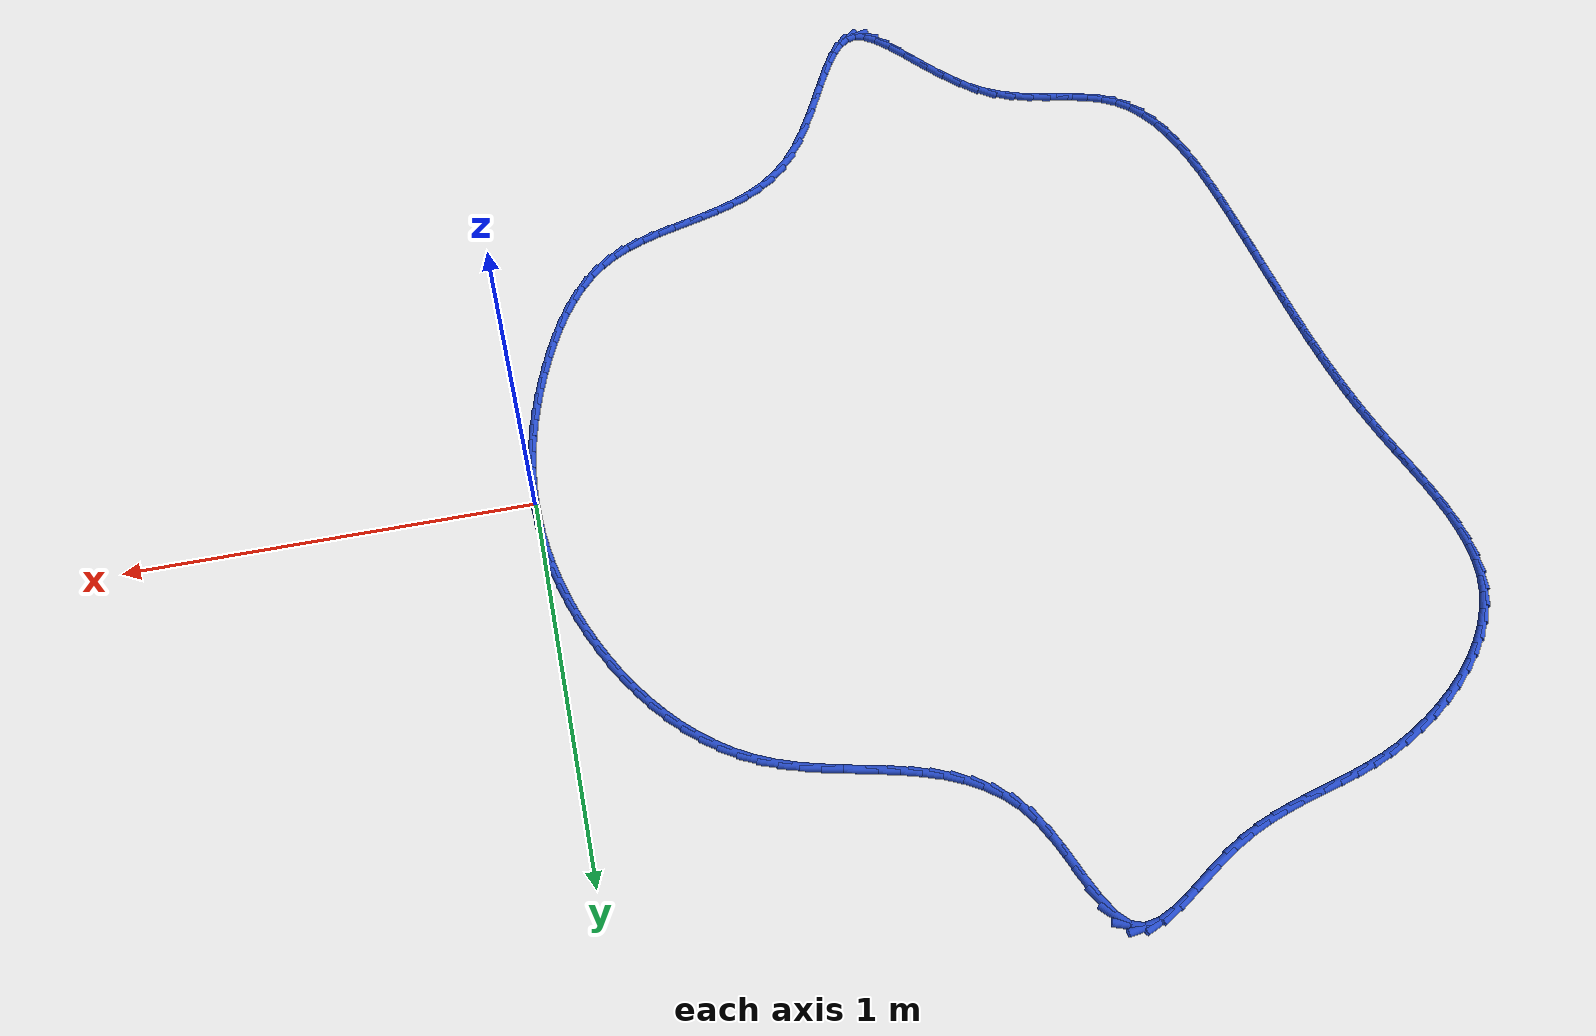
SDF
<sdf version="1.6">
 <world name="default">
  <light name="sun" type="directional">
   <pose>0 0 10 0 -0 0</pose>
   <diffuse>0.8 0.8 0.8 1</diffuse>
   <specular>0.2 0.2 0.2 1</specular>
   <attenuation>
    <range>1000</range>
    <constant>0.9</constant>
    <linear>0.01</linear>
    <quadratic>0.001</quadratic>
   </attenuation>
   <direction>-0.5 0.1 -0.9</direction>
  </light>
  <model name="ground_plane">
   <static>1</static>
   <link name="link">
    <collision name="collision">
     <geometry><plane><normal>0 0 1</normal><size>100 100</size></plane></geometry>
     <surface><friction><ode><mu>100</mu><mu2>50</mu2></ode></friction></surface>
    </collision>
    <visual name="visual">
     <cast_shadows>0</cast_shadows>
     <geometry><plane><normal>0 0 1</normal><size>100 100</size></plane></geometry>
     <material>
      <script><uri>file://media/materials/scripts/gazebo.material</uri><name>Gazebo/WhiteGlow</name></script>
     </material>
    </visual>
   </link>
  </model>
  <gravity>0 0 -9.8</gravity>
  <magnetic_field>6e-06 2.3e-05 -4.2e-05</magnetic_field>
  <atmosphere type="adiabatic"/>
  <physics name="default_physics" default="0" type="ode">
   <max_step_size>0.001</max_step_size>
   <real_time_factor>1</real_time_factor>
   <real_time_update_rate>1000</real_time_update_rate>
  </physics>
  <scene><ambient>0.4 0.4 0.4 1</ambient><background>0.7 0.7 0.7 1</background><shadows>1</shadows></scene>
  <spherical_coordinates>
   <surface_model>EARTH_WGS84</surface_model>
   <latitude_deg>0</latitude_deg>
   <longitude_deg>0</longitude_deg>
   <elevation>0</elevation>
   <heading_deg>0</heading_deg>
  </spherical_coordinates>
  <model name="line">
   <link name="link_0">
    <pose>2.0816681711721685e-17 -5.551115123125783e-17 0.01 0 1.57 -1.5523088054794187</pose>
    <collision name="collision">
     <geometry><cylinder><radius>0.01</radius><length>0.08</length></cylinder></geometry>
    </collision>
    <visual name="visual">
     <material>
      <script><name>Gazebo/Blue</name><uri>file://media/materials/scripts/gazebo.material</uri></script>
     </material>
     <geometry><cylinder><radius>0.01</radius><length>0.08</length></cylinder></geometry>
    </visual>
   </link>
   <link name="link_1">
    <pose>-0.0008562477940501431 0.04630962828117616 0.01 0 1.57 -1.5026158189526297</pose>
    <collision name="collision">
     <geometry><cylinder><radius>0.01</radius><length>0.08</length></cylinder></geometry>
    </collision>
    <visual name="visual">
     <material>
      <script><name>Gazebo/Blue</name><uri>file://media/materials/scripts/gazebo.material</uri></script>
     </material>
     <geometry><cylinder><radius>0.01</radius><length>0.08</length></cylinder></geometry>
    </visual>
   </link>
   <link name="link_2">
    <pose>-0.004022852722941298 0.09268207059834314 0.01 0 1.57 -1.453713289861988</pose>
    <collision name="collision">
     <geometry><cylinder><radius>0.01</radius><length>0.08</length></cylinder></geometry>
    </collision>
    <visual name="visual">
     <material>
      <script><name>Gazebo/Blue</name><uri>file://media/materials/scripts/gazebo.material</uri></script>
     </material>
     <geometry><cylinder><radius>0.01</radius><length>0.08</length></cylinder></geometry>
    </visual>
   </link>
   <link name="link_3">
    <pose>-0.009475367597711448 0.13903871682253485 0.01 0 1.57 -1.4055718458695168</pose>
    <collision name="collision">
     <geometry><cylinder><radius>0.01</radius><length>0.08</length></cylinder></geometry>
    </collision>
    <visual name="visual">
     <material>
      <script><name>Gazebo/Blue</name><uri>file://media/materials/scripts/gazebo.material</uri></script>
     </material>
     <geometry><cylinder><radius>0.01</radius><length>0.08</length></cylinder></geometry>
    </visual>
   </link>
   <link name="link_4">
    <pose>-0.017189345229398585 0.18530095682478506 0.01 0 1.57 -1.3581532531895133</pose>
    <collision name="collision">
     <geometry><cylinder><radius>0.01</radius><length>0.08</length></cylinder></geometry>
    </collision>
    <visual name="visual">
     <material>
      <script><name>Gazebo/Blue</name><uri>file://media/materials/scripts/gazebo.material</uri></script>
     </material>
     <geometry><cylinder><radius>0.01</radius><length>0.08</length></cylinder></geometry>
    </visual>
   </link>
   <link name="link_5">
    <pose>-0.027140338429040692 0.23139018047612792 0.01 0 1.57 -1.3114122756941347</pose>
    <collision name="collision">
     <geometry><cylinder><radius>0.01</radius><length>0.08</length></cylinder></geometry>
    </collision>
    <visual name="visual">
     <material>
      <script><name>Gazebo/Blue</name><uri>file://media/materials/scripts/gazebo.material</uri></script>
     </material>
     <geometry><cylinder><radius>0.01</radius><length>0.08</length></cylinder></geometry>
    </visual>
   </link>
   <link name="link_6">
    <pose>-0.039303900007675786 0.27722777764759726 0.01 0 1.57 -1.2652984080838954</pose>
    <collision name="collision">
     <geometry><cylinder><radius>0.01</radius><length>0.08</length></cylinder></geometry>
    </collision>
    <visual name="visual">
     <material>
      <script><name>Gazebo/Blue</name><uri>file://media/materials/scripts/gazebo.material</uri></script>
     </material>
     <geometry><cylinder><radius>0.01</radius><length>0.08</length></cylinder></geometry>
    </visual>
   </link>
   <link name="link_7">
    <pose>-0.053655582776341845 0.32273513821022715 0.01 0 1.57 -1.2197574620672487</pose>
    <collision name="collision">
     <geometry><cylinder><radius>0.01</radius><length>0.08</length></cylinder></geometry>
    </collision>
    <visual name="visual">
     <material>
      <script><name>Gazebo/Blue</name><uri>file://media/materials/scripts/gazebo.material</uri></script>
     </material>
     <geometry><cylinder><radius>0.01</radius><length>0.08</length></cylinder></geometry>
    </visual>
   </link>
   <link name="link_8">
    <pose>-0.0701709395460769 0.36783365203505153 0.01 0 1.57 -1.1746021792192476</pose>
    <collision name="collision">
     <geometry><cylinder><radius>0.01</radius><length>0.08</length></cylinder></geometry>
    </collision>
    <visual name="visual">
     <material>
      <script><name>Gazebo/Blue</name><uri>file://media/materials/scripts/gazebo.material</uri></script>
     </material>
     <geometry><cylinder><radius>0.01</radius><length>0.08</length></cylinder></geometry>
    </visual>
   </link>
   <link name="link_9">
    <pose>-0.08882763986999251 0.4124333776462103 0.01 0 1.57 -1.1281457233160899</pose>
    <collision name="collision">
     <geometry><cylinder><radius>0.01</radius><length>0.08</length></cylinder></geometry>
    </collision>
    <visual name="visual">
     <material>
      <script><name>Gazebo/Blue</name><uri>file://media/materials/scripts/gazebo.material</uri></script>
     </material>
     <geometry><cylinder><radius>0.01</radius><length>0.08</length></cylinder></geometry>
    </visual>
   </link>
   <link name="link_10">
    <pose>-0.10962780403747245 0.4563134838491791 0.01 0 1.57 -1.078931156878199</pose>
    <collision name="collision">
     <geometry><cylinder><radius>0.01</radius><length>0.08</length></cylinder></geometry>
    </collision>
    <visual name="visual">
     <material>
      <script><name>Gazebo/Blue</name><uri>file://media/materials/scripts/gazebo.material</uri></script>
     </material>
     <geometry><cylinder><radius>0.01</radius><length>0.08</length></cylinder></geometry>
    </visual>
   </link>
   <link name="link_11">
    <pose>-0.1325892530624173 0.4991690903070276 0.01 0 1.57 -1.0263862099845946</pose>
    <collision name="collision">
     <geometry><cylinder><radius>0.01</radius><length>0.08</length></cylinder></geometry>
    </collision>
    <visual name="visual">
     <material>
      <script><name>Gazebo/Blue</name><uri>file://media/materials/scripts/gazebo.material</uri></script>
     </material>
     <geometry><cylinder><radius>0.01</radius><length>0.08</length></cylinder></geometry>
    </visual>
   </link>
   <link name="link_12">
    <pose>-0.15773006633531272 0.540693933540897 0.01 0 1.57 -0.9699509158918701</pose>
    <collision name="collision">
     <geometry><cylinder><radius>0.01</radius><length>0.08</length></cylinder></geometry>
    </collision>
    <visual name="visual">
     <material>
      <script><name>Gazebo/Blue</name><uri>file://media/materials/scripts/gazebo.material</uri></script>
     </material>
     <geometry><cylinder><radius>0.01</radius><length>0.08</length></cylinder></geometry>
    </visual>
   </link>
   <link name="link_13">
    <pose>-0.1850683232466442 0.5805817500719277 0.01 0 1.57 -0.9090741819365421</pose>
    <collision name="collision">
     <geometry><cylinder><radius>0.01</radius><length>0.08</length></cylinder></geometry>
    </collision>
    <visual name="visual">
     <material>
      <script><name>Gazebo/Blue</name><uri>file://media/materials/scripts/gazebo.material</uri></script>
     </material>
     <geometry><cylinder><radius>0.01</radius><length>0.08</length></cylinder></geometry>
    </visual>
   </link>
   <link name="link_14">
    <pose>-0.21462210318689756 0.6185262764212612 0.01 0 1.57 -0.843238937741024</pose>
    <collision name="collision">
     <geometry><cylinder><radius>0.01</radius><length>0.08</length></cylinder></geometry>
    </collision>
    <visual name="visual">
     <material>
      <script><name>Gazebo/Blue</name><uri>file://media/materials/scripts/gazebo.material</uri></script>
     </material>
     <geometry><cylinder><radius>0.01</radius><length>0.08</length></cylinder></geometry>
    </visual>
   </link>
   <link name="link_15">
    <pose>-0.24640948554655828 0.6542212491100381 0.01 0 1.57 -0.7720031255314951</pose>
    <collision name="collision">
     <geometry><cylinder><radius>0.01</radius><length>0.08</length></cylinder></geometry>
    </collision>
    <visual name="visual">
     <material>
      <script><name>Gazebo/Blue</name><uri>file://media/materials/scripts/gazebo.material</uri></script>
     </material>
     <geometry><cylinder><radius>0.01</radius><length>0.08</length></cylinder></geometry>
    </visual>
   </link>
   <link name="link_16">
    <pose>-0.2804485497161122 0.6873604046593995 0.01 0 1.57 -0.6950587270388701</pose>
    <collision name="collision">
     <geometry><cylinder><radius>0.01</radius><length>0.08</length></cylinder></geometry>
    </collision>
    <visual name="visual">
     <material>
      <script><name>Gazebo/Blue</name><uri>file://media/materials/scripts/gazebo.material</uri></script>
     </material>
     <geometry><cylinder><radius>0.01</radius><length>0.08</length></cylinder></geometry>
    </visual>
   </link>
   <link name="link_17">
    <pose>-0.31675737508604485 0.7176374795904863 0.01 0 1.57 -0.6123076943201725</pose>
    <collision name="collision">
     <geometry><cylinder><radius>0.01</radius><length>0.08</length></cylinder></geometry>
    </collision>
    <visual name="visual">
     <material>
      <script><name>Gazebo/Blue</name><uri>file://media/materials/scripts/gazebo.material</uri></script>
     </material>
     <geometry><cylinder><radius>0.01</radius><length>0.08</length></cylinder></geometry>
    </visual>
   </link>
   <link name="link_18">
    <pose>-0.3553540410468418 0.7447462104244391 0.01 0 1.57 -0.5239471722190218</pose>
    <collision name="collision">
     <geometry><cylinder><radius>0.01</radius><length>0.08</length></cylinder></geometry>
    </collision>
    <visual name="visual">
     <material>
      <script><name>Gazebo/Blue</name><uri>file://media/materials/scripts/gazebo.material</uri></script>
     </material>
     <geometry><cylinder><radius>0.01</radius><length>0.08</length></cylinder></geometry>
    </visual>
   </link>
   <link name="link_19">
    <pose>-0.396256626988989 0.7683803336823997 0.01 0 1.57 -0.43117568816066637</pose>
    <collision name="collision">
     <geometry><cylinder><radius>0.01</radius><length>0.08</length></cylinder></geometry>
    </collision>
    <visual name="visual">
     <material>
      <script><name>Gazebo/Blue</name><uri>file://media/materials/scripts/gazebo.material</uri></script>
     </material>
     <geometry><cylinder><radius>0.01</radius><length>0.08</length></cylinder></geometry>
    </visual>
   </link>
   <link name="link_20">
    <pose>-0.43947029616138683 0.7882605560169792 0.01 0 1.57 -0.34804617072365196</pose>
    <collision name="collision">
     <geometry><cylinder><radius>0.01</radius><length>0.08</length></cylinder></geometry>
    </collision>
    <visual name="visual">
     <material>
      <script><name>Gazebo/Blue</name><uri>file://media/materials/scripts/gazebo.material</uri></script>
     </material>
     <geometry><cylinder><radius>0.01</radius><length>0.08</length></cylinder></geometry>
    </visual>
   </link>
   <link name="link_21">
    <pose>-0.4847260487259708 0.8046800626690344 0.01 0 1.57 -0.28691967845813743</pose>
    <collision name="collision">
     <geometry><cylinder><radius>0.01</radius><length>0.08</length></cylinder></geometry>
    </collision>
    <visual name="visual">
     <material>
      <script><name>Gazebo/Blue</name><uri>file://media/materials/scripts/gazebo.material</uri></script>
     </material>
     <geometry><cylinder><radius>0.01</radius><length>0.08</length></cylinder></geometry>
    </visual>
   </link>
   <link name="link_22">
    <pose>-0.5314928751247355 0.8184791400819844 0.01 0 1.57 -0.24708174238288394</pose>
    <collision name="collision">
     <geometry><cylinder><radius>0.01</radius><length>0.08</length></cylinder></geometry>
    </collision>
    <visual name="visual">
     <material>
      <script><name>Gazebo/Blue</name><uri>file://media/materials/scripts/gazebo.material</uri></script>
     </material>
     <geometry><cylinder><radius>0.01</radius><length>0.08</length></cylinder></geometry>
    </visual>
   </link>
   <link name="link_23">
    <pose>-0.5792292818981033 0.8305199660823602 0.01 0 1.57 -0.2273875629762651</pose>
    <collision name="collision">
     <geometry><cylinder><radius>0.01</radius><length>0.08</length></cylinder></geometry>
    </collision>
    <visual name="visual">
     <material>
      <script><name>Gazebo/Blue</name><uri>file://media/materials/scripts/gazebo.material</uri></script>
     </material>
     <geometry><cylinder><radius>0.01</radius><length>0.08</length></cylinder></geometry>
    </visual>
   </link>
   <link name="link_24">
    <pose>-0.6273937755864961 0.8416647184966923 0.01 0 1.57 -0.22723635034153497</pose>
    <collision name="collision">
     <geometry><cylinder><radius>0.01</radius><length>0.08</length></cylinder></geometry>
    </collision>
    <visual name="visual">
     <material>
      <script><name>Gazebo/Blue</name><uri>file://media/materials/scripts/gazebo.material</uri></script>
     </material>
     <geometry><cylinder><radius>0.01</radius><length>0.08</length></cylinder></geometry>
    </visual>
   </link>
   <link name="link_25">
    <pose>-0.6754448627303362 0.852775575151511 0.01 0 1.57 -0.24676687477948778</pose>
    <collision name="collision">
     <geometry><cylinder><radius>0.01</radius><length>0.08</length></cylinder></geometry>
    </collision>
    <visual name="visual">
     <material>
      <script><name>Gazebo/Blue</name><uri>file://media/materials/scripts/gazebo.material</uri></script>
     </material>
     <geometry><cylinder><radius>0.01</radius><length>0.08</length></cylinder></geometry>
    </visual>
   </link>
   <link name="link_26">
    <pose>-0.722841049870046 0.8647147138733469 0.01 0 1.57 -0.28687648122449777</pose>
    <collision name="collision">
     <geometry><cylinder><radius>0.01</radius><length>0.08</length></cylinder></geometry>
    </collision>
    <visual name="visual">
     <material>
      <script><name>Gazebo/Blue</name><uri>file://media/materials/scripts/gazebo.material</uri></script>
     </material>
     <geometry><cylinder><radius>0.01</radius><length>0.08</length></cylinder></geometry>
    </visual>
   </link>
   <link name="link_27">
    <pose>-0.7690408435460478 0.8783443124887305 0.01 0 1.57 -0.34905444501290284</pose>
    <collision name="collision">
     <geometry><cylinder><radius>0.01</radius><length>0.08</length></cylinder></geometry>
    </collision>
    <visual name="visual">
     <material>
      <script><name>Gazebo/Blue</name><uri>file://media/materials/scripts/gazebo.material</uri></script>
     </material>
     <geometry><cylinder><radius>0.01</radius><length>0.08</length></cylinder></geometry>
    </visual>
   </link>
   <link name="link_28">
    <pose>-0.8135027502987635 0.8945265488241919 0.01 0 1.57 -0.4349102155003879</pose>
    <collision name="collision">
     <geometry><cylinder><radius>0.01</radius><length>0.08</length></cylinder></geometry>
    </collision>
    <visual name="visual">
     <material>
      <script><name>Gazebo/Blue</name><uri>file://media/materials/scripts/gazebo.material</uri></script>
     </material>
     <geometry><cylinder><radius>0.01</radius><length>0.08</length></cylinder></geometry>
    </visual>
   </link>
   <link name="link_29">
    <pose>-0.8556852766686156 0.9141236007062622 0.01 0 1.57 -0.545207552889291</pose>
    <collision name="collision">
     <geometry><cylinder><radius>0.01</radius><length>0.08</length></cylinder></geometry>
    </collision>
    <visual name="visual">
     <material>
      <script><name>Gazebo/Blue</name><uri>file://media/materials/scripts/gazebo.material</uri></script>
     </material>
     <geometry><cylinder><radius>0.01</radius><length>0.08</length></cylinder></geometry>
    </visual>
   </link>
   <link name="link_30">
    <pose>-0.8950469291960258 0.9379976459614712 0.01 0 1.57 -0.6783516136781377</pose>
    <collision name="collision">
     <geometry><cylinder><radius>0.01</radius><length>0.08</length></cylinder></geometry>
    </collision>
    <visual name="visual">
     <material>
      <script><name>Gazebo/Blue</name><uri>file://media/materials/scripts/gazebo.material</uri></script>
     </material>
     <geometry><cylinder><radius>0.01</radius><length>0.08</length></cylinder></geometry>
    </visual>
   </link>
   <link name="link_31">
    <pose>-0.9310462144214172 0.9670108624163503 0.01 0 1.57 -0.8288686219652901</pose>
    <collision name="collision">
     <geometry><cylinder><radius>0.01</radius><length>0.08</length></cylinder></geometry>
    </collision>
    <visual name="visual">
     <material>
      <script><name>Gazebo/Blue</name><uri>file://media/materials/scripts/gazebo.material</uri></script>
     </material>
     <geometry><cylinder><radius>0.01</radius><length>0.08</length></cylinder></geometry>
    </visual>
   </link>
   <link name="link_32">
    <pose>-0.9631416388852112 1.0020254278974292 0.01 0 1.57 -0.9872090528609867</pose>
    <collision name="collision">
     <geometry><cylinder><radius>0.01</radius><length>0.08</length></cylinder></geometry>
    </collision>
    <visual name="visual">
     <material>
      <script><name>Gazebo/Blue</name><uri>file://media/materials/scripts/gazebo.material</uri></script>
     </material>
     <geometry><cylinder><radius>0.01</radius><length>0.08</length></cylinder></geometry>
    </visual>
   </link>
   <link name="link_33">
    <pose>-0.9907926886231171 1.0439014381811937 0.01 0 1.57 -1.1241796847085146</pose>
    <collision name="collision">
     <geometry><cylinder><radius>0.01</radius><length>0.08</length></cylinder></geometry>
    </collision>
    <visual name="visual">
     <material>
      <script><name>Gazebo/Blue</name><uri>file://media/materials/scripts/gazebo.material</uri></script>
     </material>
     <geometry><cylinder><radius>0.01</radius><length>0.08</length></cylinder></geometry>
    </visual>
   </link>
   <link name="link_34">
    <pose>-1.0139968040161436 1.0923554941402367 0.01 0 1.57 -1.1986816421628594</pose>
    <collision name="collision">
     <geometry><cylinder><radius>0.01</radius><length>0.08</length></cylinder></geometry>
    </collision>
    <visual name="visual">
     <material>
      <script><name>Gazebo/Blue</name><uri>file://media/materials/scripts/gazebo.material</uri></script>
     </material>
     <geometry><cylinder><radius>0.01</radius><length>0.08</length></cylinder></geometry>
    </visual>
   </link>
   <link name="link_35">
    <pose>-1.034179957176001 1.1440676587543366 0.01 0 1.57 -1.218198573939741</pose>
    <collision name="collision">
     <geometry><cylinder><radius>0.01</radius><length>0.08</length></cylinder></geometry>
    </collision>
    <visual name="visual">
     <material>
      <script><name>Gazebo/Blue</name><uri>file://media/materials/scripts/gazebo.material</uri></script>
     </material>
     <geometry><cylinder><radius>0.01</radius><length>0.08</length></cylinder></geometry>
    </visual>
   </link>
   <link name="link_36">
    <pose>-1.053002596469034 1.1952195839306596 0.01 0 1.57 -1.1826969173662143</pose>
    <collision name="collision">
     <geometry><cylinder><radius>0.01</radius><length>0.08</length></cylinder></geometry>
    </collision>
    <visual name="visual">
     <material>
      <script><name>Gazebo/Blue</name><uri>file://media/materials/scripts/gazebo.material</uri></script>
     </material>
     <geometry><cylinder><radius>0.01</radius><length>0.08</length></cylinder></geometry>
    </visual>
   </link>
   <link name="link_37">
    <pose>-1.0721251702615868 1.2419929215763696 0.01 0 1.57 -1.0706252050689649</pose>
    <collision name="collision">
     <geometry><cylinder><radius>0.01</radius><length>0.08</length></cylinder></geometry>
    </collision>
    <visual name="visual">
     <material>
      <script><name>Gazebo/Blue</name><uri>file://media/materials/scripts/gazebo.material</uri></script>
     </material>
     <geometry><cylinder><radius>0.01</radius><length>0.08</length></cylinder></geometry>
    </visual>
   </link>
   <link name="link_38">
    <pose>-1.0932081269200047 1.2805693235986324 0.01 0 1.57 -0.8216123796723335</pose>
    <collision name="collision">
     <geometry><cylinder><radius>0.01</radius><length>0.08</length></cylinder></geometry>
    </collision>
    <visual name="visual">
     <material>
      <script><name>Gazebo/Blue</name><uri>file://media/materials/scripts/gazebo.material</uri></script>
     </material>
     <geometry><cylinder><radius>0.01</radius><length>0.08</length></cylinder></geometry>
    </visual>
   </link>
   <link name="link_39">
    <pose>-1.1179119148106325 1.3071304419046132 0.01 0 1.57 -0.34691109677925225</pose>
    <collision name="collision">
     <geometry><cylinder><radius>0.01</radius><length>0.08</length></cylinder></geometry>
    </collision>
    <visual name="visual">
     <material>
      <script><name>Gazebo/Blue</name><uri>file://media/materials/scripts/gazebo.material</uri></script>
     </material>
     <geometry><cylinder><radius>0.01</radius><length>0.08</length></cylinder></geometry>
    </visual>
   </link>
   <link name="link_40">
    <pose>-1.1478602824353137 1.3179577333398131 0.01 0 1.57 0.14723987993688775</pose>
    <collision name="collision">
     <geometry><cylinder><radius>0.01</radius><length>0.08</length></cylinder></geometry>
    </collision>
    <visual name="visual">
     <material>
      <script><name>Gazebo/Blue</name><uri>file://media/materials/scripts/gazebo.material</uri></script>
     </material>
     <geometry><cylinder><radius>0.01</radius><length>0.08</length></cylinder></geometry>
    </visual>
   </link>
   <link name="link_41">
    <pose>-1.1834461508242995 1.3126798785496088 0.01 0 1.57 0.4152922864736502</pose>
    <collision name="collision">
     <geometry><cylinder><radius>0.01</radius><length>0.08</length></cylinder></geometry>
    </collision>
    <visual name="visual">
     <material>
      <script><name>Gazebo/Blue</name><uri>file://media/materials/scripts/gazebo.material</uri></script>
     </material>
     <geometry><cylinder><radius>0.01</radius><length>0.08</length></cylinder></geometry>
    </visual>
   </link>
   <link name="link_42">
    <pose>-1.223568455358852 1.2949884381819365 0.01 0 1.57 0.5419102771159844</pose>
    <collision name="collision">
     <geometry><cylinder><radius>0.01</radius><length>0.08</length></cylinder></geometry>
    </collision>
    <visual name="visual">
     <material>
      <script><name>Gazebo/Blue</name><uri>file://media/materials/scripts/gazebo.material</uri></script>
     </material>
     <geometry><cylinder><radius>0.01</radius><length>0.08</length></cylinder></geometry>
    </visual>
   </link>
   <link name="link_43">
    <pose>-1.2670361797257603 1.2688195956767516 0.01 0 1.57 0.5924704917500305</pose>
    <collision name="collision">
     <geometry><cylinder><radius>0.01</radius><length>0.08</length></cylinder></geometry>
    </collision>
    <visual name="visual">
     <material>
      <script><name>Gazebo/Blue</name><uri>file://media/materials/scripts/gazebo.material</uri></script>
     </material>
     <geometry><cylinder><radius>0.01</radius><length>0.08</length></cylinder></geometry>
    </visual>
   </link>
   <link name="link_44">
    <pose>-1.3126583076118121 1.2381095344740076 0.01 0 1.57 0.5918282268407821</pose>
    <collision name="collision">
     <geometry><cylinder><radius>0.01</radius><length>0.08</length></cylinder></geometry>
    </collision>
    <visual name="visual">
     <material>
      <script><name>Gazebo/Blue</name><uri>file://media/materials/scripts/gazebo.material</uri></script>
     </material>
     <geometry><cylinder><radius>0.01</radius><length>0.08</length></cylinder></geometry>
    </visual>
   </link>
   <link name="link_45">
    <pose>-1.3592438227037944 1.2067944380136586 0.01 0 1.57 0.5440300993520716</pose>
    <collision name="collision">
     <geometry><cylinder><radius>0.01</radius><length>0.08</length></cylinder></geometry>
    </collision>
    <visual name="visual">
     <material>
      <script><name>Gazebo/Blue</name><uri>file://media/materials/scripts/gazebo.material</uri></script>
     </material>
     <geometry><cylinder><radius>0.01</radius><length>0.08</length></cylinder></geometry>
    </visual>
   </link>
   <link name="link_46">
    <pose>-1.4056209008960523 1.1787399649979278 0.01 0 1.57 0.4687645041360836</pose>
    <collision name="collision">
     <geometry><cylinder><radius>0.01</radius><length>0.08</length></cylinder></geometry>
    </collision>
    <visual name="visual">
     <material>
      <script><name>Gazebo/Blue</name><uri>file://media/materials/scripts/gazebo.material</uri></script>
     </material>
     <geometry><cylinder><radius>0.01</radius><length>0.08</length></cylinder></geometry>
    </visual>
   </link>
   <link name="link_47">
    <pose>-1.4512044041170242 1.1556559054744895 0.01 0 1.57 0.3986505613362843</pose>
    <collision name="collision">
     <geometry><cylinder><radius>0.01</radius><length>0.08</length></cylinder></geometry>
    </collision>
    <visual name="visual">
     <material>
      <script><name>Gazebo/Blue</name><uri>file://media/materials/scripts/gazebo.material</uri></script>
     </material>
     <geometry><cylinder><radius>0.01</radius><length>0.08</length></cylinder></geometry>
    </visual>
   </link>
   <link name="link_48">
    <pose>-1.4960901188673854 1.1367498867394121 0.01 0 1.57 0.3396456490612573</pose>
    <collision name="collision">
     <geometry><cylinder><radius>0.01</radius><length>0.08</length></cylinder></geometry>
    </collision>
    <visual name="visual">
     <material>
      <script><name>Gazebo/Blue</name><uri>file://media/materials/scripts/gazebo.material</uri></script>
     </material>
     <geometry><cylinder><radius>0.01</radius><length>0.08</length></cylinder></geometry>
    </visual>
   </link>
   <link name="link_49">
    <pose>-1.540412002763732 1.1210892704142041 0.01 0 1.57 0.29522009134099886</pose>
    <collision name="collision">
     <geometry><cylinder><radius>0.01</radius><length>0.08</length></cylinder></geometry>
    </collision>
    <visual name="visual">
     <material>
      <script><name>Gazebo/Blue</name><uri>file://media/materials/scripts/gazebo.material</uri></script>
     </material>
     <geometry><cylinder><radius>0.01</radius><length>0.08</length></cylinder></geometry>
    </visual>
   </link>
   <link name="link_50">
    <pose>-1.5843040134226627 1.1077414181203746 0.01 0 1.57 0.2679140729212931</pose>
    <collision name="collision">
     <geometry><cylinder><radius>0.01</radius><length>0.08</length></cylinder></geometry>
    </collision>
    <visual name="visual">
     <material>
      <script><name>Gazebo/Blue</name><uri>file://media/materials/scripts/gazebo.material</uri></script>
     </material>
     <geometry><cylinder><radius>0.01</radius><length>0.08</length></cylinder></geometry>
    </visual>
   </link>
   <link name="link_51">
    <pose>-1.6279001084607747 1.095773691479432 0.01 0 1.57 0.25926499721534324</pose>
    <collision name="collision">
     <geometry><cylinder><radius>0.01</radius><length>0.08</length></cylinder></geometry>
    </collision>
    <visual name="visual">
     <material>
      <script><name>Gazebo/Blue</name><uri>file://media/materials/scripts/gazebo.material</uri></script>
     </material>
     <geometry><cylinder><radius>0.01</radius><length>0.08</length></cylinder></geometry>
    </visual>
   </link>
   <link name="link_52">
    <pose>-1.671334245494664 1.0842534521128848 0.01 0 1.57 0.26983712389195036</pose>
    <collision name="collision">
     <geometry><cylinder><radius>0.01</radius><length>0.08</length></cylinder></geometry>
    </collision>
    <visual name="visual">
     <material>
      <script><name>Gazebo/Blue</name><uri>file://media/materials/scripts/gazebo.material</uri></script>
     </material>
     <geometry><cylinder><radius>0.01</radius><length>0.08</length></cylinder></geometry>
    </visual>
   </link>
   <link name="link_53">
    <pose>-1.7147403821409293 1.0722480616422416 0.01 0 1.57 0.2992302851891857</pose>
    <collision name="collision">
     <geometry><cylinder><radius>0.01</radius><length>0.08</length></cylinder></geometry>
    </collision>
    <visual name="visual">
     <material>
      <script><name>Gazebo/Blue</name><uri>file://media/materials/scripts/gazebo.material</uri></script>
     </material>
     <geometry><cylinder><radius>0.01</radius><length>0.08</length></cylinder></geometry>
    </visual>
   </link>
   <link name="link_54">
    <pose>-1.7582524760161675 1.0588248816890113 0.01 0 1.57 0.34601854716499</pose>
    <collision name="collision">
     <geometry><cylinder><radius>0.01</radius><length>0.08</length></cylinder></geometry>
    </collision>
    <visual name="visual">
     <material>
      <script><name>Gazebo/Blue</name><uri>file://media/materials/scripts/gazebo.material</uri></script>
     </material>
     <geometry><cylinder><radius>0.01</radius><length>0.08</length></cylinder></geometry>
    </visual>
   </link>
   <link name="link_55">
    <pose>-1.8020044847369758 1.0430512738747026 0.01 0 1.57 0.40609576984024304</pose>
    <collision name="collision">
     <geometry><cylinder><radius>0.01</radius><length>0.08</length></cylinder></geometry>
    </collision>
    <visual name="visual">
     <material>
      <script><name>Gazebo/Blue</name><uri>file://media/materials/scripts/gazebo.material</uri></script>
     </material>
     <geometry><cylinder><radius>0.01</radius><length>0.08</length></cylinder></geometry>
    </visual>
   </link>
   <link name="link_56">
    <pose>-1.8460593371289398 1.0241078068059202 0.01 0 1.57 0.46761730242271554</pose>
    <collision name="collision">
     <geometry><cylinder><radius>0.01</radius><length>0.08</length></cylinder></geometry>
    </collision>
    <visual name="visual">
     <material>
      <script><name>Gazebo/Blue</name><uri>file://media/materials/scripts/gazebo.material</uri></script>
     </material>
     <geometry><cylinder><radius>0.01</radius><length>0.08</length></cylinder></geometry>
    </visual>
   </link>
   <link name="link_57">
    <pose>-1.890019304321067 1.0019092537441263 0.01 0 1.57 0.5280268091726366</pose>
    <collision name="collision">
     <geometry><cylinder><radius>0.01</radius><length>0.08</length></cylinder></geometry>
    </collision>
    <visual name="visual">
     <material>
      <script><name>Gazebo/Blue</name><uri>file://media/materials/scripts/gazebo.material</uri></script>
     </material>
     <geometry><cylinder><radius>0.01</radius><length>0.08</length></cylinder></geometry>
    </visual>
   </link>
   <link name="link_58">
    <pose>-1.933302910636562 0.9766632469676643 0.01 0 1.57 0.5891253522813282</pose>
    <collision name="collision">
     <geometry><cylinder><radius>0.01</radius><length>0.08</length></cylinder></geometry>
    </collision>
    <visual name="visual">
     <material>
      <script><name>Gazebo/Blue</name><uri>file://media/materials/scripts/gazebo.material</uri></script>
     </material>
     <geometry><cylinder><radius>0.01</radius><length>0.08</length></cylinder></geometry>
    </visual>
   </link>
   <link name="link_59">
    <pose>-1.9753282027525287 0.9485781800359614 0.01 0 1.57 0.6526268983144646</pose>
    <collision name="collision">
     <geometry><cylinder><radius>0.01</radius><length>0.08</length></cylinder></geometry>
    </collision>
    <visual name="visual">
     <material>
      <script><name>Gazebo/Blue</name><uri>file://media/materials/scripts/gazebo.material</uri></script>
     </material>
     <geometry><cylinder><radius>0.01</radius><length>0.08</length></cylinder></geometry>
    </visual>
   </link>
   <link name="link_60">
    <pose>-2.015513227346071 0.9178624465084436 0.01 0 1.57 0.7202613249780546</pose>
    <collision name="collision">
     <geometry><cylinder><radius>0.01</radius><length>0.08</length></cylinder></geometry>
    </collision>
    <visual name="visual">
     <material>
      <script><name>Gazebo/Blue</name><uri>file://media/materials/scripts/gazebo.material</uri></script>
     </material>
     <geometry><cylinder><radius>0.01</radius><length>0.08</length></cylinder></geometry>
    </visual>
   </link>
   <link name="link_61">
    <pose>-2.0532760310942932 0.8847244399445371 0.01 0 1.57 0.7938596944100431</pose>
    <collision name="collision">
     <geometry><cylinder><radius>0.01</radius><length>0.08</length></cylinder></geometry>
    </collision>
    <visual name="visual">
     <material>
      <script><name>Gazebo/Blue</name><uri>file://media/materials/scripts/gazebo.material</uri></script>
     </material>
     <geometry><cylinder><radius>0.01</radius><length>0.08</length></cylinder></geometry>
    </visual>
   </link>
   <link name="link_62">
    <pose>-2.088034660674298 0.8493725539036686 0.01 0 1.57 0.8754050287475194</pose>
    <collision name="collision">
     <geometry><cylinder><radius>0.01</radius><length>0.08</length></cylinder></geometry>
    </collision>
    <visual name="visual">
     <material>
      <script><name>Gazebo/Blue</name><uri>file://media/materials/scripts/gazebo.material</uri></script>
     </material>
     <geometry><cylinder><radius>0.01</radius><length>0.08</length></cylinder></geometry>
    </visual>
   </link>
   <link name="link_63">
    <pose>-2.11920716276319 0.8120151819452643 0.01 0 1.57 0.9670237591008793</pose>
    <collision name="collision">
     <geometry><cylinder><radius>0.01</radius><length>0.08</length></cylinder></geometry>
    </collision>
    <visual name="visual">
     <material>
      <script><name>Gazebo/Blue</name><uri>file://media/materials/scripts/gazebo.material</uri></script>
     </material>
     <geometry><cylinder><radius>0.01</radius><length>0.08</length></cylinder></geometry>
    </visual>
   </link>
   <link name="link_64">
    <pose>-2.146211584038072 0.772860717628751 0.01 0 1.57 1.0708663506252771</pose>
    <collision name="collision">
     <geometry><cylinder><radius>0.01</radius><length>0.08</length></cylinder></geometry>
    </collision>
    <visual name="visual">
     <material>
      <script><name>Gazebo/Blue</name><uri>file://media/materials/scripts/gazebo.material</uri></script>
     </material>
     <geometry><cylinder><radius>0.01</radius><length>0.08</length></cylinder></geometry>
    </visual>
   </link>
   <link name="link_65">
    <pose>-2.1684659711760483 0.7321175545135546 0.01 0 1.57 1.188796624749201</pose>
    <collision name="collision">
     <geometry><cylinder><radius>0.01</radius><length>0.08</length></cylinder></geometry>
    </collision>
    <visual name="visual">
     <material>
      <script><name>Gazebo/Blue</name><uri>file://media/materials/scripts/gazebo.material</uri></script>
     </material>
     <geometry><cylinder><radius>0.01</radius><length>0.08</length></cylinder></geometry>
    </visual>
   </link>
   <link name="link_66">
    <pose>-2.185388370854223 0.6899940861591018 0.01 0 1.57 1.3217451869023198</pose>
    <collision name="collision">
     <geometry><cylinder><radius>0.01</radius><length>0.08</length></cylinder></geometry>
    </collision>
    <visual name="visual">
     <material>
      <script><name>Gazebo/Blue</name><uri>file://media/materials/scripts/gazebo.material</uri></script>
     </material>
     <geometry><cylinder><radius>0.01</radius><length>0.08</length></cylinder></geometry>
    </visual>
   </link>
   <link name="link_67">
    <pose>-2.1963997730639138 0.6466986045191268 0.01 0 1.57 1.4596288669667246</pose>
    <collision name="collision">
     <geometry><cylinder><radius>0.01</radius><length>0.08</length></cylinder></geometry>
    </collision>
    <visual name="visual">
     <material>
      <script><name>Gazebo/Blue</name><uri>file://media/materials/scripts/gazebo.material</uri></script>
     </material>
     <geometry><cylinder><radius>0.01</radius><length>0.08</length></cylinder></geometry>
    </visual>
   </link>
   <link name="link_68">
    <pose>-2.201341946600214 0.6024248759076204 0.01 0 1.57 -1.5612426031239126</pose>
    <collision name="collision">
     <geometry><cylinder><radius>0.01</radius><length>0.08</length></cylinder></geometry>
    </collision>
    <visual name="visual">
     <material>
      <script><name>Gazebo/Blue</name><uri>file://media/materials/scripts/gazebo.material</uri></script>
     </material>
     <geometry><cylinder><radius>0.01</radius><length>0.08</length></cylinder></geometry>
    </visual>
   </link>
   <link name="link_69">
    <pose>-2.2009111779915496 0.5573371679646039 0.01 0 1.57 -1.461834718123281</pose>
    <collision name="collision">
     <geometry><cylinder><radius>0.01</radius><length>0.08</length></cylinder></geometry>
    </collision>
    <visual name="visual">
     <material>
      <script><name>Gazebo/Blue</name><uri>file://media/materials/scripts/gazebo.material</uri></script>
     </material>
     <geometry><cylinder><radius>0.01</radius><length>0.08</length></cylinder></geometry>
    </visual>
   </link>
   <link name="link_70">
    <pose>-2.195907346937747 0.5115961722063144 0.01 0 1.57 -1.383188211248397</pose>
    <collision name="collision">
     <geometry><cylinder><radius>0.01</radius><length>0.08</length></cylinder></geometry>
    </collision>
    <visual name="visual">
     <material>
      <script><name>Gazebo/Blue</name><uri>file://media/materials/scripts/gazebo.material</uri></script>
     </material>
     <geometry><cylinder><radius>0.01</radius><length>0.08</length></cylinder></geometry>
    </visual>
   </link>
   <link name="link_71">
    <pose>-2.1871303331386307 0.46536258014898896 0.01 0 1.57 -1.3236169426747946</pose>
    <collision name="collision">
     <geometry><cylinder><radius>0.01</radius><length>0.08</length></cylinder></geometry>
    </collision>
    <visual name="visual">
     <material>
      <script><name>Gazebo/Blue</name><uri>file://media/materials/scripts/gazebo.material</uri></script>
     </material>
     <geometry><cylinder><radius>0.01</radius><length>0.08</length></cylinder></geometry>
    </visual>
   </link>
   <link name="link_72">
    <pose>-2.175380016294028 0.41879708330886595 0.01 0 1.57 -1.2812500685947474</pose>
    <collision name="collision">
     <geometry><cylinder><radius>0.01</radius><length>0.08</length></cylinder></geometry>
    </collision>
    <visual name="visual">
     <material>
      <script><name>Gazebo/Blue</name><uri>file://media/materials/scripts/gazebo.material</uri></script>
     </material>
     <geometry><cylinder><radius>0.01</radius><length>0.08</length></cylinder></geometry>
    </visual>
   </link>
   <link name="link_73">
    <pose>-2.161456276103763 0.37206037320218194 0.01 0 1.57 -1.2545451766551847</pose>
    <collision name="collision">
     <geometry><cylinder><radius>0.01</radius><length>0.08</length></cylinder></geometry>
    </collision>
    <visual name="visual">
     <material>
      <script><name>Gazebo/Blue</name><uri>file://media/materials/scripts/gazebo.material</uri></script>
     </material>
     <geometry><cylinder><radius>0.01</radius><length>0.08</length></cylinder></geometry>
    </visual>
   </link>
   <link name="link_74">
    <pose>-2.146158992267662 0.3253131413451754 0.01 0 1.57 -1.2425203136314507</pose>
    <collision name="collision">
     <geometry><cylinder><radius>0.01</radius><length>0.08</length></cylinder></geometry>
    </collision>
    <visual name="visual">
     <material>
      <script><name>Gazebo/Blue</name><uri>file://media/materials/scripts/gazebo.material</uri></script>
     </material>
     <geometry><cylinder><radius>0.01</radius><length>0.08</length></cylinder></geometry>
    </visual>
   </link>
   <link name="link_75">
    <pose>-2.1302880444855514 0.27871607925408337 0.01 0 1.57 -1.244851743325411</pose>
    <collision name="collision">
     <geometry><cylinder><radius>0.01</radius><length>0.08</length></cylinder></geometry>
    </collision>
    <visual name="visual">
     <material>
      <script><name>Gazebo/Blue</name><uri>file://media/materials/scripts/gazebo.material</uri></script>
     </material>
     <geometry><cylinder><radius>0.01</radius><length>0.08</length></cylinder></geometry>
    </visual>
   </link>
   <link name="link_76">
    <pose>-2.1146433124572557 0.23242987844514296 0.01 0 1.57 -1.2614977414646271</pose>
    <collision name="collision">
     <geometry><cylinder><radius>0.01</radius><length>0.08</length></cylinder></geometry>
    </collision>
    <visual name="visual">
     <material>
      <script><name>Gazebo/Blue</name><uri>file://media/materials/scripts/gazebo.material</uri></script>
     </material>
     <geometry><cylinder><radius>0.01</radius><length>0.08</length></cylinder></geometry>
    </visual>
   </link>
   <link name="link_77">
    <pose>-2.100000878461082 0.18660845041135654 0.01 0 1.57 -1.2848748387831703</pose>
    <collision name="collision">
     <geometry><cylinder><radius>0.01</radius><length>0.08</length></cylinder></geometry>
    </collision>
    <visual name="visual">
     <material>
      <script><name>Gazebo/Blue</name><uri>file://media/materials/scripts/gazebo.material</uri></script>
     </material>
     <geometry><cylinder><radius>0.01</radius><length>0.08</length></cylinder></geometry>
    </visual>
   </link>
   <link name="link_78">
    <pose>-2.0866735326945123 0.14127371204830438 0.01 0 1.57 -1.3073966854616528</pose>
    <collision name="collision">
     <geometry><cylinder><radius>0.01</radius><length>0.08</length></cylinder></geometry>
    </collision>
    <visual name="visual">
     <material>
      <script><name>Gazebo/Blue</name><uri>file://media/materials/scripts/gazebo.material</uri></script>
     </material>
     <geometry><cylinder><radius>0.01</radius><length>0.08</length></cylinder></geometry>
    </visual>
   </link>
   <link name="link_79">
    <pose>-2.074553152038147 0.0963276596094735 0.01 0 1.57 -1.3285190304848364</pose>
    <collision name="collision">
     <geometry><cylinder><radius>0.01</radius><length>0.08</length></cylinder></geometry>
    </collision>
    <visual name="visual">
     <material>
      <script><name>Gazebo/Blue</name><uri>file://media/materials/scripts/gazebo.material</uri></script>
     </material>
     <geometry><cylinder><radius>0.01</radius><length>0.08</length></cylinder></geometry>
    </visual>
   </link>
   <link name="link_80">
    <pose>-2.063516316162767 0.05166793108466314 0.01 0 1.57 -1.3479915256226258</pose>
    <collision name="collision">
     <geometry><cylinder><radius>0.01</radius><length>0.08</length></cylinder></geometry>
    </collision>
    <visual name="visual">
     <material>
      <script><name>Gazebo/Blue</name><uri>file://media/materials/scripts/gazebo.material</uri></script>
     </material>
     <geometry><cylinder><radius>0.01</radius><length>0.08</length></cylinder></geometry>
    </visual>
   </link>
   <link name="link_81">
    <pose>-2.0534396047391534 0.007192164463672855 0.01 0 1.57 -1.3655904365540195</pose>
    <collision name="collision">
     <geometry><cylinder><radius>0.01</radius><length>0.08</length></cylinder></geometry>
    </collision>
    <visual name="visual">
     <material>
      <script><name>Gazebo/Blue</name><uri>file://media/materials/scripts/gazebo.material</uri></script>
     </material>
     <geometry><cylinder><radius>0.01</radius><length>0.08</length></cylinder></geometry>
    </visual>
   </link>
   <link name="link_82">
    <pose>-2.044199597438086 -0.03720200226369862 0.01 0 1.57 -1.381125247913184</pose>
    <collision name="collision">
     <geometry><cylinder><radius>0.01</radius><length>0.08</length></cylinder></geometry>
    </collision>
    <visual name="visual">
     <material>
      <script><name>Gazebo/Blue</name><uri>file://media/materials/scripts/gazebo.material</uri></script>
     </material>
     <geometry><cylinder><radius>0.01</radius><length>0.08</length></cylinder></geometry>
    </visual>
   </link>
   <link name="link_83">
    <pose>-2.035672873930345 -0.08161693110765009 0.01 0 1.57 -1.3944435489759759</pose>
    <collision name="collision">
     <geometry><cylinder><radius>0.01</radius><length>0.08</length></cylinder></geometry>
    </collision>
    <visual name="visual">
     <material>
      <script><name>Gazebo/Blue</name><uri>file://media/materials/scripts/gazebo.material</uri></script>
     </material>
     <geometry><cylinder><radius>0.01</radius><length>0.08</length></cylinder></geometry>
    </visual>
   </link>
   <link name="link_84">
    <pose>-2.027736013886709 -0.12615498407838283 0.01 0 1.57 -1.405434057671806</pose>
    <collision name="collision">
     <geometry><cylinder><radius>0.01</radius><length>0.08</length></cylinder></geometry>
    </collision>
    <visual name="visual">
     <material>
      <script><name>Gazebo/Blue</name><uri>file://media/materials/scripts/gazebo.material</uri></script>
     </material>
     <geometry><cylinder><radius>0.01</radius><length>0.08</length></cylinder></geometry>
    </visual>
   </link>
   <link name="link_85">
    <pose>-2.0202655969779606 -0.1709185231860973 0.01 0 1.57 -1.4140278137770619</pose>
    <collision name="collision">
     <geometry><cylinder><radius>0.01</radius><length>0.08</length></cylinder></geometry>
    </collision>
    <visual name="visual">
     <material>
      <script><name>Gazebo/Blue</name><uri>file://media/materials/scripts/gazebo.material</uri></script>
     </material>
     <geometry><cylinder><radius>0.01</radius><length>0.08</length></cylinder></geometry>
    </visual>
   </link>
   <link name="link_86">
    <pose>-2.0131382028748788 -0.21600991044099396 0.01 0 1.57 -1.4201977074869372</pose>
    <collision name="collision">
     <geometry><cylinder><radius>0.01</radius><length>0.08</length></cylinder></geometry>
    </collision>
    <visual name="visual">
     <material>
      <script><name>Gazebo/Blue</name><uri>file://media/materials/scripts/gazebo.material</uri></script>
     </material>
     <geometry><cylinder><radius>0.01</radius><length>0.08</length></cylinder></geometry>
    </visual>
   </link>
   <link name="link_87">
    <pose>-2.006230411248243 -0.26153150785327395 0.01 0 1.57 -1.4239565959583875</pose>
    <collision name="collision">
     <geometry><cylinder><radius>0.01</radius><length>0.08</length></cylinder></geometry>
    </collision>
    <visual name="visual">
     <material>
      <script><name>Gazebo/Blue</name><uri>file://media/materials/scripts/gazebo.material</uri></script>
     </material>
     <geometry><cylinder><radius>0.01</radius><length>0.08</length></cylinder></geometry>
    </visual>
   </link>
   <link name="link_88">
    <pose>-1.9994188017688346 -0.3075856774331362 0.01 0 1.57 -1.4253542988864354</pose>
    <collision name="collision">
     <geometry><cylinder><radius>0.01</radius><length>0.08</length></cylinder></geometry>
    </collision>
    <visual name="visual">
     <material>
      <script><name>Gazebo/Blue</name><uri>file://media/materials/scripts/gazebo.material</uri></script>
     </material>
     <geometry><cylinder><radius>0.01</radius><length>0.08</length></cylinder></geometry>
    </visual>
   </link>
   <link name="link_89">
    <pose>-1.9925799541074334 -0.35427478119078204 0.01 0 1.57 -1.4244737642878313</pose>
    <collision name="collision">
     <geometry><cylinder><radius>0.01</radius><length>0.08</length></cylinder></geometry>
    </collision>
    <visual name="visual">
     <material>
      <script><name>Gazebo/Blue</name><uri>file://media/materials/scripts/gazebo.material</uri></script>
     </material>
     <geometry><cylinder><radius>0.01</radius><length>0.08</length></cylinder></geometry>
    </visual>
   </link>
   <link name="link_90">
    <pose>-1.985590447934819 -0.4017011811364116 0.01 0 1.57 -1.421426670872112</pose>
    <collision name="collision">
     <geometry><cylinder><radius>0.01</radius><length>0.08</length></cylinder></geometry>
    </collision>
    <visual name="visual">
     <material>
      <script><name>Gazebo/Blue</name><uri>file://media/materials/scripts/gazebo.material</uri></script>
     </material>
     <geometry><cylinder><radius>0.01</radius><length>0.08</length></cylinder></geometry>
    </visual>
   </link>
   <link name="link_91">
    <pose>-1.9783268629217723 -0.4499672392802257 0.01 0 1.57 -1.4163486968567365</pose>
    <collision name="collision">
     <geometry><cylinder><radius>0.01</radius><length>0.08</length></cylinder></geometry>
    </collision>
    <visual name="visual">
     <material>
      <script><name>Gazebo/Blue</name><uri>file://media/materials/scripts/gazebo.material</uri></script>
     </material>
     <geometry><cylinder><radius>0.01</radius><length>0.08</length></cylinder></geometry>
    </visual>
   </link>
   <link name="link_92">
    <pose>-1.970665778739073 -0.49917531763242534 0.01 0 1.57 -1.4093946470042429</pose>
    <collision name="collision">
     <geometry><cylinder><radius>0.01</radius><length>0.08</length></cylinder></geometry>
    </collision>
    <visual name="visual">
     <material>
      <script><name>Gazebo/Blue</name><uri>file://media/materials/scripts/gazebo.material</uri></script>
     </material>
     <geometry><cylinder><radius>0.01</radius><length>0.08</length></cylinder></geometry>
    </visual>
   </link>
   <link name="link_93">
    <pose>-1.962483775057501 -0.5494277782032095 0.01 0 1.57 -1.399506362370498</pose>
    <collision name="collision">
     <geometry><cylinder><radius>0.01</radius><length>0.08</length></cylinder></geometry>
    </collision>
    <visual name="visual">
     <material>
      <script><name>Gazebo/Blue</name><uri>file://media/materials/scripts/gazebo.material</uri></script>
     </material>
     <geometry><cylinder><radius>0.01</radius><length>0.08</length></cylinder></geometry>
    </visual>
   </link>
   <link name="link_94">
    <pose>-1.9536160949088475 -0.6006904625494014 0.01 0 1.57 -1.3814141704852922</pose>
    <collision name="collision">
     <geometry><cylinder><radius>0.01</radius><length>0.08</length></cylinder></geometry>
    </collision>
    <visual name="visual">
     <material>
      <script><name>Gazebo/Blue</name><uri>file://media/materials/scripts/gazebo.material</uri></script>
     </material>
     <geometry><cylinder><radius>0.01</radius><length>0.08</length></cylinder></geometry>
    </visual>
   </link>
   <link name="link_95">
    <pose>-1.9437173566021355 -0.6523326719757379 0.01 0 1.57 -1.3532350472329695</pose>
    <collision name="collision">
     <geometry><cylinder><radius>0.01</radius><length>0.08</length></cylinder></geometry>
    </collision>
    <visual name="visual">
     <material>
      <script><name>Gazebo/Blue</name><uri>file://media/materials/scripts/gazebo.material</uri></script>
     </material>
     <geometry><cylinder><radius>0.01</radius><length>0.08</length></cylinder></geometry>
    </visual>
   </link>
   <link name="link_96">
    <pose>-1.9323928562752772 -0.7035608139154147 0.01 0 1.57 -1.3138151033967536</pose>
    <collision name="collision">
     <geometry><cylinder><radius>0.01</radius><length>0.08</length></cylinder></geometry>
    </collision>
    <visual name="visual">
     <material>
      <script><name>Gazebo/Blue</name><uri>file://media/materials/scripts/gazebo.material</uri></script>
     </material>
     <geometry><cylinder><radius>0.01</radius><length>0.08</length></cylinder></geometry>
    </visual>
   </link>
   <link name="link_97">
    <pose>-1.9192478889119724 -0.7535812919896606 0.01 0 1.57 -1.2612069243431632</pose>
    <collision name="collision">
     <geometry><cylinder><radius>0.01</radius><length>0.08</length></cylinder></geometry>
    </collision>
    <visual name="visual">
     <material>
      <script><name>Gazebo/Blue</name><uri>file://media/materials/scripts/gazebo.material</uri></script>
     </material>
     <geometry><cylinder><radius>0.01</radius><length>0.08</length></cylinder></geometry>
    </visual>
   </link>
   <link name="link_98">
    <pose>-1.9038877494959205 -0.8016005098197068 0.01 0 1.57 -1.1925742919951654</pose>
    <collision name="collision">
     <geometry><cylinder><radius>0.01</radius><length>0.08</length></cylinder></geometry>
    </collision>
    <visual name="visual">
     <material>
      <script><name>Gazebo/Blue</name><uri>file://media/materials/scripts/gazebo.material</uri></script>
     </material>
     <geometry><cylinder><radius>0.01</radius><length>0.08</length></cylinder></geometry>
    </visual>
   </link>
   <link name="link_99">
    <pose>-1.8859177330108192 -0.8468248710267829 0.01 0 1.57 -1.1041434538485544</pose>
    <collision name="collision">
     <geometry><cylinder><radius>0.01</radius><length>0.08</length></cylinder></geometry>
    </collision>
    <visual name="visual">
     <material>
      <script><name>Gazebo/Blue</name><uri>file://media/materials/scripts/gazebo.material</uri></script>
     </material>
     <geometry><cylinder><radius>0.01</radius><length>0.08</length></cylinder></geometry>
    </visual>
   </link>
   <link name="link_100">
    <pose>-1.8649431344403693 -0.8884607792321201 0.01 0 1.57 -0.9914288974655863</pose>
    <collision name="collision">
     <geometry><cylinder><radius>0.01</radius><length>0.08</length></cylinder></geometry>
    </collision>
    <visual name="visual">
     <material>
      <script><name>Gazebo/Blue</name><uri>file://media/materials/scripts/gazebo.material</uri></script>
     </material>
     <geometry><cylinder><radius>0.01</radius><length>0.08</length></cylinder></geometry>
    </visual>
   </link>
   <link name="link_101">
    <pose>-1.8405692487682674 -0.9257146380569486 0.01 0 1.57 -0.8502132893631668</pose>
    <collision name="collision">
     <geometry><cylinder><radius>0.01</radius><length>0.08</length></cylinder></geometry>
    </collision>
    <visual name="visual">
     <material>
      <script><name>Gazebo/Blue</name><uri>file://media/materials/scripts/gazebo.material</uri></script>
     </material>
     <geometry><cylinder><radius>0.01</radius><length>0.08</length></cylinder></geometry>
    </visual>
   </link>
   <link name="link_102">
    <pose>-1.812401370978215 -0.9577928511224976 0.01 0 1.57 -0.6789425558330618</pose>
    <collision name="collision">
     <geometry><cylinder><radius>0.01</radius><length>0.08</length></cylinder></geometry>
    </collision>
    <visual name="visual">
     <material>
      <script><name>Gazebo/Blue</name><uri>file://media/materials/scripts/gazebo.material</uri></script>
     </material>
     <geometry><cylinder><radius>0.01</radius><length>0.08</length></cylinder></geometry>
    </visual>
   </link>
   <link name="link_103">
    <pose>-1.7800447960539092 -0.9839018220499978 0.01 0 1.57 -0.48816862874105477</pose>
    <collision name="collision">
     <geometry><cylinder><radius>0.01</radius><length>0.08</length></cylinder></geometry>
    </collision>
    <visual name="visual">
     <material>
      <script><name>Gazebo/Blue</name><uri>file://media/materials/scripts/gazebo.material</uri></script>
     </material>
     <geometry><cylinder><radius>0.01</radius><length>0.08</length></cylinder></geometry>
    </visual>
   </link>
   <link name="link_104">
    <pose>-1.7432074370436421 -1.0034638609020714 0.01 0 1.57 -0.3337459284437555</pose>
    <collision name="collision">
     <geometry><cylinder><radius>0.01</radius><length>0.08</length></cylinder></geometry>
    </collision>
    <visual name="visual">
     <material>
      <script><name>Gazebo/Blue</name><uri>file://media/materials/scripts/gazebo.material</uri></script>
     </material>
     <geometry><cylinder><radius>0.01</radius><length>0.08</length></cylinder></geometry>
    </visual>
   </link>
   <link name="link_105">
    <pose>-1.7024090179417157 -1.0176093124147085 0.01 0 1.57 -0.23869276200514036</pose>
    <collision name="collision">
     <geometry><cylinder><radius>0.01</radius><length>0.08</length></cylinder></geometry>
    </collision>
    <visual name="visual">
     <material>
      <script><name>Gazebo/Blue</name><uri>file://media/materials/scripts/gazebo.material</uri></script>
     </material>
     <geometry><cylinder><radius>0.01</radius><length>0.08</length></cylinder></geometry>
    </visual>
   </link>
   <link name="link_106">
    <pose>-1.658555117830301 -1.0282803530344893 0.01 0 1.57 -0.19621319979628593</pose>
    <collision name="collision">
     <geometry><cylinder><radius>0.01</radius><length>0.08</length></cylinder></geometry>
    </collision>
    <visual name="visual">
     <material>
      <script><name>Gazebo/Blue</name><uri>file://media/materials/scripts/gazebo.material</uri></script>
     </material>
     <geometry><cylinder><radius>0.01</radius><length>0.08</length></cylinder></geometry>
    </visual>
   </link>
   <link name="link_107">
    <pose>-1.6125536602918662 -1.037424091991686 0.01 0 1.57 -0.19974182880665384</pose>
    <collision name="collision">
     <geometry><cylinder><radius>0.01</radius><length>0.08</length></cylinder></geometry>
    </collision>
    <visual name="visual">
     <material>
      <script><name>Gazebo/Blue</name><uri>file://media/materials/scripts/gazebo.material</uri></script>
     </material>
     <geometry><cylinder><radius>0.01</radius><length>0.08</length></cylinder></geometry>
    </visual>
   </link>
   <link name="link_108">
    <pose>-1.5653125689088792 -1.0469876385165715 0.01 0 1.57 -0.245715733587195</pose>
    <collision name="collision">
     <geometry><cylinder><radius>0.01</radius><length>0.08</length></cylinder></geometry>
    </collision>
    <visual name="visual">
     <material>
      <script><name>Gazebo/Blue</name><uri>file://media/materials/scripts/gazebo.material</uri></script>
     </material>
     <geometry><cylinder><radius>0.01</radius><length>0.08</length></cylinder></geometry>
    </visual>
   </link>
   <link name="link_109">
    <pose>-1.5177397672638067 -1.0589181018394187 0.01 0 1.57 -0.33279655130228775</pose>
    <collision name="collision">
     <geometry><cylinder><radius>0.01</radius><length>0.08</length></cylinder></geometry>
    </collision>
    <visual name="visual">
     <material>
      <script><name>Gazebo/Blue</name><uri>file://media/materials/scripts/gazebo.material</uri></script>
     </material>
     <geometry><cylinder><radius>0.01</radius><length>0.08</length></cylinder></geometry>
    </visual>
   </link>
   <link name="link_110">
    <pose>-1.4707431789391157 -1.0751625911905003 0.01 0 1.57 -0.4592329466374295</pose>
    <collision name="collision">
     <geometry><cylinder><radius>0.01</radius><length>0.08</length></cylinder></geometry>
    </collision>
    <visual name="visual">
     <material>
      <script><name>Gazebo/Blue</name><uri>file://media/materials/scripts/gazebo.material</uri></script>
     </material>
     <geometry><cylinder><radius>0.01</radius><length>0.08</length></cylinder></geometry>
    </visual>
   </link>
   <link name="link_111">
    <pose>-1.425230727517273 -1.0976682158000897 0.01 0 1.57 -0.6108309820504617</pose>
    <collision name="collision">
     <geometry><cylinder><radius>0.01</radius><length>0.08</length></cylinder></geometry>
    </collision>
    <visual name="visual">
     <material>
      <script><name>Gazebo/Blue</name><uri>file://media/materials/scripts/gazebo.material</uri></script>
     </material>
     <geometry><cylinder><radius>0.01</radius><length>0.08</length></cylinder></geometry>
    </visual>
   </link>
   <link name="link_112">
    <pose>-1.382009092843484 -1.127930123731113 0.01 0 1.57 -0.7308542162275113</pose>
    <collision name="collision">
     <geometry><cylinder><radius>0.01</radius><length>0.08</length></cylinder></geometry>
    </collision>
    <visual name="visual">
     <material>
      <script><name>Gazebo/Blue</name><uri>file://media/materials/scripts/gazebo.material</uri></script>
     </material>
     <geometry><cylinder><radius>0.01</radius><length>0.08</length></cylinder></geometry>
    </visual>
   </link>
   <link name="link_113">
    <pose>-1.3412238705600072 -1.1644923235869094 0.01 0 1.57 -0.8076782384119696</pose>
    <collision name="collision">
     <geometry><cylinder><radius>0.01</radius><length>0.08</length></cylinder></geometry>
    </collision>
    <visual name="visual">
     <material>
      <script><name>Gazebo/Blue</name><uri>file://media/materials/scripts/gazebo.material</uri></script>
     </material>
     <geometry><cylinder><radius>0.01</radius><length>0.08</length></cylinder></geometry>
    </visual>
   </link>
   <link name="link_114">
    <pose>-1.3027553306258153 -1.2047143862091723 0.01 0 1.57 -0.8493794196460572</pose>
    <collision name="collision">
     <geometry><cylinder><radius>0.01</radius><length>0.08</length></cylinder></geometry>
    </collision>
    <visual name="visual">
     <material>
      <script><name>Gazebo/Blue</name><uri>file://media/materials/scripts/gazebo.material</uri></script>
     </material>
     <geometry><cylinder><radius>0.01</radius><length>0.08</length></cylinder></geometry>
    </visual>
   </link>
   <link name="link_115">
    <pose>-1.2664830284501822 -1.2459526926253421 0.01 0 1.57 -0.8586257522154652</pose>
    <collision name="collision">
     <geometry><cylinder><radius>0.01</radius><length>0.08</length></cylinder></geometry>
    </collision>
    <visual name="visual">
     <material>
      <script><name>Gazebo/Blue</name><uri>file://media/materials/scripts/gazebo.material</uri></script>
     </material>
     <geometry><cylinder><radius>0.01</radius><length>0.08</length></cylinder></geometry>
    </visual>
   </link>
   <link name="link_116">
    <pose>-1.2322865194423802 -1.2855636238628596 0.01 0 1.57 -0.8312187820102228</pose>
    <collision name="collision">
     <geometry><cylinder><radius>0.01</radius><length>0.08</length></cylinder></geometry>
    </collision>
    <visual name="visual">
     <material>
      <script><name>Gazebo/Blue</name><uri>file://media/materials/scripts/gazebo.material</uri></script>
     </material>
     <geometry><cylinder><radius>0.01</radius><length>0.08</length></cylinder></geometry>
    </visual>
   </link>
   <link name="link_117">
    <pose>-1.2000453590116837 -1.320903560949164 0.01 0 1.57 -0.7517396359911928</pose>
    <collision name="collision">
     <geometry><cylinder><radius>0.01</radius><length>0.08</length></cylinder></geometry>
    </collision>
    <visual name="visual">
     <material>
      <script><name>Gazebo/Blue</name><uri>file://media/materials/scripts/gazebo.material</uri></script>
     </material>
     <geometry><cylinder><radius>0.01</radius><length>0.08</length></cylinder></geometry>
    </visual>
   </link>
   <link name="link_118">
    <pose>-1.1696391025673656 -1.3493288849116967 0.01 0 1.57 -0.5816839639103729</pose>
    <collision name="collision">
     <geometry><cylinder><radius>0.01</radius><length>0.08</length></cylinder></geometry>
    </collision>
    <visual name="visual">
     <material>
      <script><name>Gazebo/Blue</name><uri>file://media/materials/scripts/gazebo.material</uri></script>
     </material>
     <geometry><cylinder><radius>0.01</radius><length>0.08</length></cylinder></geometry>
    </visual>
   </link>
   <link name="link_119">
    <pose>-1.1409473055186994 -1.3681959767778982 0.01 0 1.57 -0.2413865208786741</pose>
    <collision name="collision">
     <geometry><cylinder><radius>0.01</radius><length>0.08</length></cylinder></geometry>
    </collision>
    <visual name="visual">
     <material>
      <script><name>Gazebo/Blue</name><uri>file://media/materials/scripts/gazebo.material</uri></script>
     </material>
     <geometry><cylinder><radius>0.01</radius><length>0.08</length></cylinder></geometry>
    </visual>
   </link>
   <link name="link_120">
    <pose>-1.11384914530739 -1.3748671849579472 0.01 0 1.57 0.2617078314445778</pose>
    <collision name="collision">
     <geometry><cylinder><radius>0.01</radius><length>0.08</length></cylinder></geometry>
    </collision>
    <visual name="visual">
     <material>
      <script><name>Gazebo/Blue</name><uri>file://media/materials/scripts/gazebo.material</uri></script>
     </material>
     <geometry><cylinder><radius>0.01</radius><length>0.08</length></cylinder></geometry>
    </visual>
   </link>
   <link name="link_121">
    <pose>-1.0881429226713335 -1.3679817458469021 0.01 0 1.57 0.6544374377137387</pose>
    <collision name="collision">
     <geometry><cylinder><radius>0.01</radius><length>0.08</length></cylinder></geometry>
    </collision>
    <visual name="visual">
     <material>
      <script><name>Gazebo/Blue</name><uri>file://media/materials/scripts/gazebo.material</uri></script>
     </material>
     <geometry><cylinder><radius>0.01</radius><length>0.08</length></cylinder></geometry>
    </visual>
   </link>
   <link name="link_122">
    <pose>-1.0634461232225836 -1.3490336197689499 0.01 0 1.57 0.8797225625496233</pose>
    <collision name="collision">
     <geometry><cylinder><radius>0.01</radius><length>0.08</length></cylinder></geometry>
    </collision>
    <visual name="visual">
     <material>
      <script><name>Gazebo/Blue</name><uri>file://media/materials/scripts/gazebo.material</uri></script>
     </material>
     <geometry><cylinder><radius>0.01</radius><length>0.08</length></cylinder></geometry>
    </visual>
   </link>
   <link name="link_123">
    <pose>-1.039351709886055 -1.3199039332295113 0.01 0 1.57 1.0025492758608119</pose>
    <collision name="collision">
     <geometry><cylinder><radius>0.01</radius><length>0.08</length></cylinder></geometry>
    </collision>
    <visual name="visual">
     <material>
      <script><name>Gazebo/Blue</name><uri>file://media/materials/scripts/gazebo.material</uri></script>
     </material>
     <geometry><cylinder><radius>0.01</radius><length>0.08</length></cylinder></geometry>
    </visual>
   </link>
   <link name="link_124">
    <pose>-1.0154526455866613 -1.2824738127340056 0.01 0 1.57 1.068065758040364</pose>
    <collision name="collision">
     <geometry><cylinder><radius>0.01</radius><length>0.08</length></cylinder></geometry>
    </collision>
    <visual name="visual">
     <material>
      <script><name>Gazebo/Blue</name><uri>file://media/materials/scripts/gazebo.material</uri></script>
     </material>
     <geometry><cylinder><radius>0.01</radius><length>0.08</length></cylinder></geometry>
    </visual>
   </link>
   <link name="link_125">
    <pose>-0.9913418932493169 -1.2386243847878533 0.01 0 1.57 1.0983316243918173</pose>
    <collision name="collision">
     <geometry><cylinder><radius>0.01</radius><length>0.08</length></cylinder></geometry>
    </collision>
    <visual name="visual">
     <material>
      <script><name>Gazebo/Blue</name><uri>file://media/materials/scripts/gazebo.material</uri></script>
     </material>
     <geometry><cylinder><radius>0.01</radius><length>0.08</length></cylinder></geometry>
    </visual>
   </link>
   <link name="link_126">
    <pose>-0.9666124157989363 -1.1902367758964734 0.01 0 1.57 1.1035051223098473</pose>
    <collision name="collision">
     <geometry><cylinder><radius>0.01</radius><length>0.08</length></cylinder></geometry>
    </collision>
    <visual name="visual">
     <material>
      <script><name>Gazebo/Blue</name><uri>file://media/materials/scripts/gazebo.material</uri></script>
     </material>
     <geometry><cylinder><radius>0.01</radius><length>0.08</length></cylinder></geometry>
    </visual>
   </link>
   <link name="link_127">
    <pose>-0.9408571761604345 -1.1391921125652884 0.01 0 1.57 1.087618206343686</pose>
    <collision name="collision">
     <geometry><cylinder><radius>0.01</radius><length>0.08</length></cylinder></geometry>
    </collision>
    <visual name="visual">
     <material>
      <script><name>Gazebo/Blue</name><uri>file://media/materials/scripts/gazebo.material</uri></script>
     </material>
     <geometry><cylinder><radius>0.01</radius><length>0.08</length></cylinder></geometry>
    </visual>
   </link>
   <link name="link_128">
    <pose>-0.9136691372587252 -1.087371521299717 0.01 0 1.57 1.0509422052948945</pose>
    <collision name="collision">
     <geometry><cylinder><radius>0.01</radius><length>0.08</length></cylinder></geometry>
    </collision>
    <visual name="visual">
     <material>
      <script><name>Gazebo/Blue</name><uri>file://media/materials/scripts/gazebo.material</uri></script>
     </material>
     <geometry><cylinder><radius>0.01</radius><length>0.08</length></cylinder></geometry>
    </visual>
   </link>
   <link name="link_129">
    <pose>-0.8846412620187237 -1.0366561286051799 0.01 0 1.57 0.99073520829271</pose>
    <collision name="collision">
     <geometry><cylinder><radius>0.01</radius><length>0.08</length></cylinder></geometry>
    </collision>
    <visual name="visual">
     <material>
      <script><name>Gazebo/Blue</name><uri>file://media/materials/scripts/gazebo.material</uri></script>
     </material>
     <geometry><cylinder><radius>0.01</radius><length>0.08</length></cylinder></geometry>
    </visual>
   </link>
   <link name="link_130">
    <pose>-0.8533665133653432 -0.9889270609870967 0.01 0 1.57 0.9012069144530354</pose>
    <collision name="collision">
     <geometry><cylinder><radius>0.01</radius><length>0.08</length></cylinder></geometry>
    </collision>
    <visual name="visual">
     <material>
      <script><name>Gazebo/Blue</name><uri>file://media/materials/scripts/gazebo.material</uri></script>
     </material>
     <geometry><cylinder><radius>0.01</radius><length>0.08</length></cylinder></geometry>
    </visual>
   </link>
   <link name="link_131">
    <pose>-0.8194378542234982 -0.9460654449508873 0.01 0 1.57 0.7767578707547819</pose>
    <collision name="collision">
     <geometry><cylinder><radius>0.01</radius><length>0.08</length></cylinder></geometry>
    </collision>
    <visual name="visual">
     <material>
      <script><name>Gazebo/Blue</name><uri>file://media/materials/scripts/gazebo.material</uri></script>
     </material>
     <geometry><cylinder><radius>0.01</radius><length>0.08</length></cylinder></geometry>
    </visual>
   </link>
   <link name="link_132">
    <pose>-0.7825070832546311 -0.9097674080574178 0.01 0 1.57 0.643394105081678</pose>
    <collision name="collision">
     <geometry><cylinder><radius>0.01</radius><length>0.08</length></cylinder></geometry>
    </collision>
    <visual name="visual">
     <material>
      <script><name>Gazebo/Blue</name><uri>file://media/materials/scripts/gazebo.material</uri></script>
     </material>
     <geometry><cylinder><radius>0.01</radius><length>0.08</length></cylinder></geometry>
    </visual>
   </link>
   <link name="link_133">
    <pose>-0.742782151771765 -0.8799803506546805 0.01 0 1.57 0.5243094415963878</pose>
    <collision name="collision">
     <geometry><cylinder><radius>0.01</radius><length>0.08</length></cylinder></geometry>
    </collision>
    <visual name="visual">
     <material>
      <script><name>Gazebo/Blue</name><uri>file://media/materials/scripts/gazebo.material</uri></script>
     </material>
     <geometry><cylinder><radius>0.01</radius><length>0.08</length></cylinder></geometry>
    </visual>
   </link>
   <link name="link_134">
    <pose>-0.7007771871432054 -0.8556889546746332 0.01 0 1.57 0.4252380161447753</pose>
    <collision name="collision">
     <geometry><cylinder><radius>0.01</radius><length>0.08</length></cylinder></geometry>
    </collision>
    <visual name="visual">
     <material>
      <script><name>Gazebo/Blue</name><uri>file://media/materials/scripts/gazebo.material</uri></script>
     </material>
     <geometry><cylinder><radius>0.01</radius><length>0.08</length></cylinder></geometry>
    </visual>
   </link>
   <link name="link_135">
    <pose>-0.6570095023776551 -0.8358678853460237 0.01 0 1.57 0.3489216940498696</pose>
    <collision name="collision">
     <geometry><cylinder><radius>0.01</radius><length>0.08</length></cylinder></geometry>
    </collision>
    <visual name="visual">
     <material>
      <script><name>Gazebo/Blue</name><uri>file://media/materials/scripts/gazebo.material</uri></script>
     </material>
     <geometry><cylinder><radius>0.01</radius><length>0.08</length></cylinder></geometry>
    </visual>
   </link>
   <link name="link_136">
    <pose>-0.611996410483816 -0.819491807897599 0.01 0 1.57 0.2961447910962637</pose>
    <collision name="collision">
     <geometry><cylinder><radius>0.01</radius><length>0.08</length></cylinder></geometry>
    </collision>
    <visual name="visual">
     <material>
      <script><name>Gazebo/Blue</name><uri>file://media/materials/scripts/gazebo.material</uri></script>
     </material>
     <geometry><cylinder><radius>0.01</radius><length>0.08</length></cylinder></geometry>
    </visual>
   </link>
   <link name="link_137">
    <pose>-0.5662552244703923 -0.8055353875581069 0.01 0 1.57 0.26685440914228514</pose>
    <collision name="collision">
     <geometry><cylinder><radius>0.01</radius><length>0.08</length></cylinder></geometry>
    </collision>
    <visual name="visual">
     <material>
      <script><name>Gazebo/Blue</name><uri>file://media/materials/scripts/gazebo.material</uri></script>
     </material>
     <geometry><cylinder><radius>0.01</radius><length>0.08</length></cylinder></geometry>
    </visual>
   </link>
   <link name="link_138">
    <pose>-0.5203032573460854 -0.792973289556294 0.01 0 1.57 0.26103175148674895</pose>
    <collision name="collision">
     <geometry><cylinder><radius>0.01</radius><length>0.08</length></cylinder></geometry>
    </collision>
    <visual name="visual">
     <material>
      <script><name>Gazebo/Blue</name><uri>file://media/materials/scripts/gazebo.material</uri></script>
     </material>
     <geometry><cylinder><radius>0.01</radius><length>0.08</length></cylinder></geometry>
    </visual>
   </link>
   <link name="link_139">
    <pose>-0.474657822119598 -0.7807801791209081 0.01 0 1.57 0.27919234634828644</pose>
    <collision name="collision">
     <geometry><cylinder><radius>0.01</radius><length>0.08</length></cylinder></geometry>
    </collision>
    <visual name="visual">
     <material>
      <script><name>Gazebo/Blue</name><uri>file://media/materials/scripts/gazebo.material</uri></script>
     </material>
     <geometry><cylinder><radius>0.01</radius><length>0.08</length></cylinder></geometry>
    </visual>
   </link>
   <link name="link_140">
    <pose>-0.42983623179963254 -0.7679307214806961 0.01 0 1.57 0.3225299192450575</pose>
    <collision name="collision">
     <geometry><cylinder><radius>0.01</radius><length>0.08</length></cylinder></geometry>
    </collision>
    <visual name="visual">
     <material>
      <script><name>Gazebo/Blue</name><uri>file://media/materials/scripts/gazebo.material</uri></script>
     </material>
     <geometry><cylinder><radius>0.01</radius><length>0.08</length></cylinder></geometry>
    </visual>
   </link>
   <link name="link_141">
    <pose>-0.3863557993948909 -0.7533995818644051 0.01 0 1.57 0.3926534608593946</pose>
    <collision name="collision">
     <geometry><cylinder><radius>0.01</radius><length>0.08</length></cylinder></geometry>
    </collision>
    <visual name="visual">
     <material>
      <script><name>Gazebo/Blue</name><uri>file://media/materials/scripts/gazebo.material</uri></script>
     </material>
     <geometry><cylinder><radius>0.01</radius><length>0.08</length></cylinder></geometry>
    </visual>
   </link>
   <link name="link_142">
    <pose>-0.34473383791407686 -0.7361614255007828 0.01 0 1.57 0.4907348958206931</pose>
    <collision name="collision">
     <geometry><cylinder><radius>0.01</radius><length>0.08</length></cylinder></geometry>
    </collision>
    <visual name="visual">
     <material>
      <script><name>Gazebo/Blue</name><uri>file://media/materials/scripts/gazebo.material</uri></script>
     </material>
     <geometry><cylinder><radius>0.01</radius><length>0.08</length></cylinder></geometry>
    </visual>
   </link>
   <link name="link_143">
    <pose>-0.30548766036589237 -0.715190917618576 0.01 0 1.57 0.6139997040571826</pose>
    <collision name="collision">
     <geometry><cylinder><radius>0.01</radius><length>0.08</length></cylinder></geometry>
    </collision>
    <visual name="visual">
     <material>
      <script><name>Gazebo/Blue</name><uri>file://media/materials/scripts/gazebo.material</uri></script>
     </material>
     <geometry><cylinder><radius>0.01</radius><length>0.08</length></cylinder></geometry>
    </visual>
   </link>
   <link name="link_144">
    <pose>-0.26910139356400764 -0.6895426349965675 0.01 0 1.57 0.7367811838941292</pose>
    <collision name="collision">
     <geometry><cylinder><radius>0.01</radius><length>0.08</length></cylinder></geometry>
    </collision>
    <visual name="visual">
     <material>
      <script><name>Gazebo/Blue</name><uri>file://media/materials/scripts/gazebo.material</uri></script>
     </material>
     <geometry><cylinder><radius>0.01</radius><length>0.08</length></cylinder></geometry>
    </visual>
   </link>
   <link name="link_145">
    <pose>-0.23566840844505318 -0.6592120850562218 0.01 0 1.57 0.843196722444265</pose>
    <collision name="collision">
     <geometry><cylinder><radius>0.01</radius><length>0.08</length></cylinder></geometry>
    </collision>
    <visual name="visual">
     <material>
      <script><name>Gazebo/Blue</name><uri>file://media/materials/scripts/gazebo.material</uri></script>
     </material>
     <geometry><cylinder><radius>0.01</radius><length>0.08</length></cylinder></geometry>
    </visual>
   </link>
   <link name="link_146">
    <pose>-0.20502759694558262 -0.6248075544583137 0.01 0 1.57 0.933762189071692</pose>
    <collision name="collision">
     <geometry><cylinder><radius>0.01</radius><length>0.08</length></cylinder></geometry>
    </collision>
    <visual name="visual">
     <material>
      <script><name>Gazebo/Blue</name><uri>file://media/materials/scripts/gazebo.material</uri></script>
     </material>
     <geometry><cylinder><radius>0.01</radius><length>0.08</length></cylinder></geometry>
    </visual>
   </link>
   <link name="link_147">
    <pose>-0.17701350153655712 -0.586947803270928 0.01 0 1.57 1.0101198781755745</pose>
    <collision name="collision">
     <geometry><cylinder><radius>0.01</radius><length>0.08</length></cylinder></geometry>
    </collision>
    <visual name="visual">
     <material>
      <script><name>Gazebo/Blue</name><uri>file://media/materials/scripts/gazebo.material</uri></script>
     </material>
     <geometry><cylinder><radius>0.01</radius><length>0.08</length></cylinder></geometry>
    </visual>
   </link>
   <link name="link_148">
    <pose>-0.15146066468893618 -0.546251591562146 0.01 0 1.57 1.0741574007701413</pose>
    <collision name="collision">
     <geometry><cylinder><radius>0.01</radius><length>0.08</length></cylinder></geometry>
    </collision>
    <visual name="visual">
     <material>
      <script><name>Gazebo/Blue</name><uri>file://media/materials/scripts/gazebo.material</uri></script>
     </material>
     <geometry><cylinder><radius>0.01</radius><length>0.08</length></cylinder></geometry>
    </visual>
   </link>
   <link name="link_149">
    <pose>-0.12820362887367961 -0.5033376794000498 0.01 0 1.57 1.1276580409319605</pose>
    <collision name="collision">
     <geometry><cylinder><radius>0.01</radius><length>0.08</length></cylinder></geometry>
    </collision>
    <visual name="visual">
     <material>
      <script><name>Gazebo/Blue</name><uri>file://media/materials/scripts/gazebo.material</uri></script>
     </material>
     <geometry><cylinder><radius>0.01</radius><length>0.08</length></cylinder></geometry>
    </visual>
   </link>
   <link name="link_150">
    <pose>-0.10707693656174758 -0.4588248268527222 0.01 0 1.57 1.1721460808478517</pose>
    <collision name="collision">
     <geometry><cylinder><radius>0.01</radius><length>0.08</length></cylinder></geometry>
    </collision>
    <visual name="visual">
     <material>
      <script><name>Gazebo/Blue</name><uri>file://media/materials/scripts/gazebo.material</uri></script>
     </material>
     <geometry><cylinder><radius>0.01</radius><length>0.08</length></cylinder></geometry>
    </visual>
   </link>
   <link name="link_151">
    <pose>-0.08791513022409958 -0.4133317939882445 0.01 0 1.57 1.208893662913475</pose>
    <collision name="collision">
     <geometry><cylinder><radius>0.01</radius><length>0.08</length></cylinder></geometry>
    </collision>
    <visual name="visual">
     <material>
      <script><name>Gazebo/Blue</name><uri>file://media/materials/scripts/gazebo.material</uri></script>
     </material>
     <geometry><cylinder><radius>0.01</radius><length>0.08</length></cylinder></geometry>
    </visual>
   </link>
   <link name="link_152">
    <pose>-0.07055422865688127 -0.3674734403270615 0.01 0 1.57 1.242145391680138</pose>
    <collision name="collision">
     <geometry><cylinder><radius>0.01</radius><length>0.08</length></cylinder></geometry>
    </collision>
    <visual name="visual">
     <material>
      <script><name>Gazebo/Blue</name><uri>file://media/materials/scripts/gazebo.material</uri></script>
     </material>
     <geometry><cylinder><radius>0.01</radius><length>0.08</length></cylinder></geometry>
    </visual>
   </link>
   <link name="link_153">
    <pose>-0.05491996224916763 -0.32162760149705344 0.01 0 1.57 1.2774424456819216</pose>
    <collision name="collision">
     <geometry><cylinder><radius>0.01</radius><length>0.08</length></cylinder></geometry>
    </collision>
    <visual name="visual">
     <material>
      <script><name>Gazebo/Blue</name><uri>file://media/materials/scripts/gazebo.material</uri></script>
     </material>
     <geometry><cylinder><radius>0.01</radius><length>0.08</length></cylinder></geometry>
    </visual>
   </link>
   <link name="link_154">
    <pose>-0.04107776924217418 -0.2758029958486783 0.01 0 1.57 1.3152499110427764</pose>
    <collision name="collision">
     <geometry><cylinder><radius>0.01</radius><length>0.08</length></cylinder></geometry>
    </collision>
    <visual name="visual">
     <material>
      <script><name>Gazebo/Blue</name><uri>file://media/materials/scripts/gazebo.material</uri></script>
     </material>
     <geometry><cylinder><radius>0.01</radius><length>0.08</length></cylinder></geometry>
    </visual>
   </link>
   <link name="link_155">
    <pose>-0.029105182624912764 -0.22997638661813743 0.01 0 1.57 1.3555353044711596</pose>
    <collision name="collision">
     <geometry><cylinder><radius>0.01</radius><length>0.08</length></cylinder></geometry>
    </collision>
    <visual name="visual">
     <material>
      <script><name>Gazebo/Blue</name><uri>file://media/materials/scripts/gazebo.material</uri></script>
     </material>
     <geometry><cylinder><radius>0.01</radius><length>0.08</length></cylinder></geometry>
    </visual>
   </link>
   <link name="link_156">
    <pose>-0.01907973538639505 -0.1841245370416317 0.01 0 1.57 1.3982225838928344</pose>
    <collision name="collision">
     <geometry><cylinder><radius>0.01</radius><length>0.08</length></cylinder></geometry>
    </collision>
    <visual name="visual">
     <material>
      <script><name>Gazebo/Blue</name><uri>file://media/materials/scripts/gazebo.material</uri></script>
     </material>
     <geometry><cylinder><radius>0.01</radius><length>0.08</length></cylinder></geometry>
    </visual>
   </link>
   <link name="link_157">
    <pose>-0.011078960515633198 -0.13822421035536409 0.01 0 1.57 1.4431857984300132</pose>
    <collision name="collision">
     <geometry><cylinder><radius>0.01</radius><length>0.08</length></cylinder></geometry>
    </collision>
    <visual name="visual">
     <material>
      <script><name>Gazebo/Blue</name><uri>file://media/materials/scripts/gazebo.material</uri></script>
     </material>
     <geometry><cylinder><radius>0.01</radius><length>0.08</length></cylinder></geometry>
    </visual>
   </link>
   <link name="link_158">
    <pose>-0.005180391001638861 -0.09225216979553541 0.01 0 1.57 1.4902444122730711</pose>
    <collision name="collision">
     <geometry><cylinder><radius>0.01</radius><length>0.08</length></cylinder></geometry>
    </collision>
    <visual name="visual">
     <material>
      <script><name>Gazebo/Blue</name><uri>file://media/materials/scripts/gazebo.material</uri></script>
     </material>
     <geometry><cylinder><radius>0.01</radius><length>0.08</length></cylinder></geometry>
    </visual>
   </link>
   <link name="link_159">
    <pose>-0.0014615598334238493 -0.04618517859834695 0.01 0 1.57 1.5391612378080506</pose>
    <collision name="collision">
     <geometry><cylinder><radius>0.01</radius><length>0.08</length></cylinder></geometry>
    </collision>
    <visual name="visual">
     <material>
      <script><name>Gazebo/Blue</name><uri>file://media/materials/scripts/gazebo.material</uri></script>
     </material>
     <geometry><cylinder><radius>0.01</radius><length>0.08</length></cylinder></geometry>
    </visual>
   </link>
   <link name="link_160">
    <pose>1.214306433183765e-17 -2.220446049250313e-16 0.01 0 1.57 -1.55194881725671</pose>
    <collision name="collision">
     <geometry><cylinder><radius>0.01</radius><length>0.08</length></cylinder></geometry>
    </collision>
    <visual name="visual">
     <material>
      <script><name>Gazebo/Blue</name><uri>file://media/materials/scripts/gazebo.material</uri></script>
     </material>
     <geometry><cylinder><radius>0.01</radius><length>0.08</length></cylinder></geometry>
    </visual>
   </link>
   <link name="link_161">
    <pose>-0.0008732444903791423 0.04632660276330407 0.01 0 1.57 -1.5519488172567097</pose>
    <collision name="collision">
     <geometry><cylinder><radius>0.01</radius><length>0.08</length></cylinder></geometry>
    </collision>
    <visual name="visual">
     <material>
      <script><name>Gazebo/Blue</name><uri>file://media/materials/scripts/gazebo.material</uri></script>
     </material>
     <geometry><cylinder><radius>0.01</radius><length>0.08</length></cylinder></geometry>
    </visual>
   </link>
  </model>
 </world>
</sdf>
